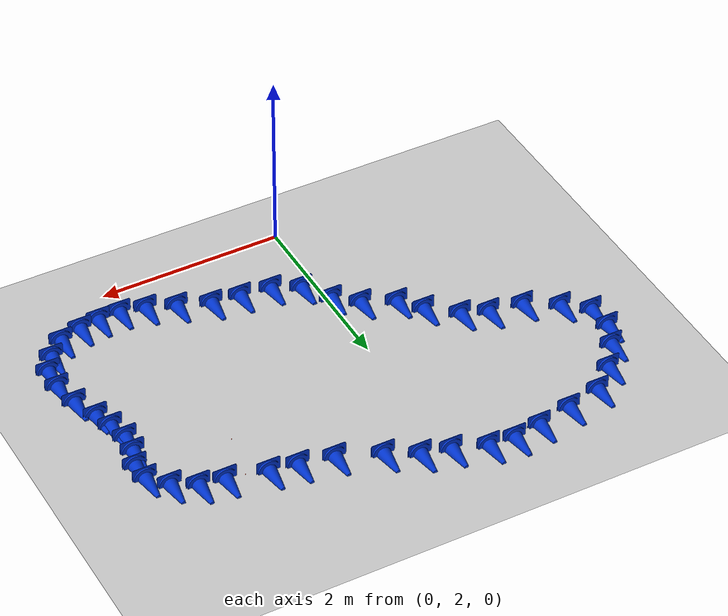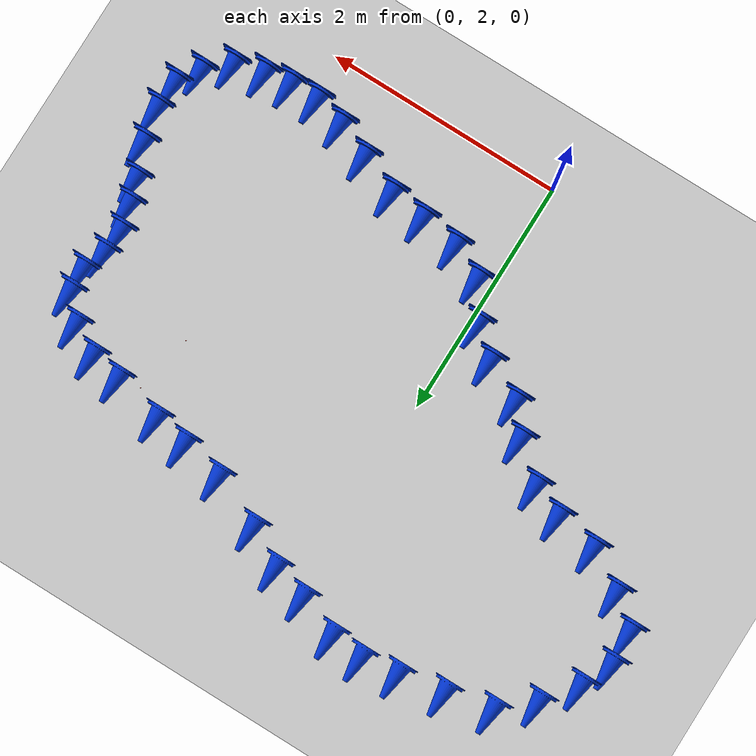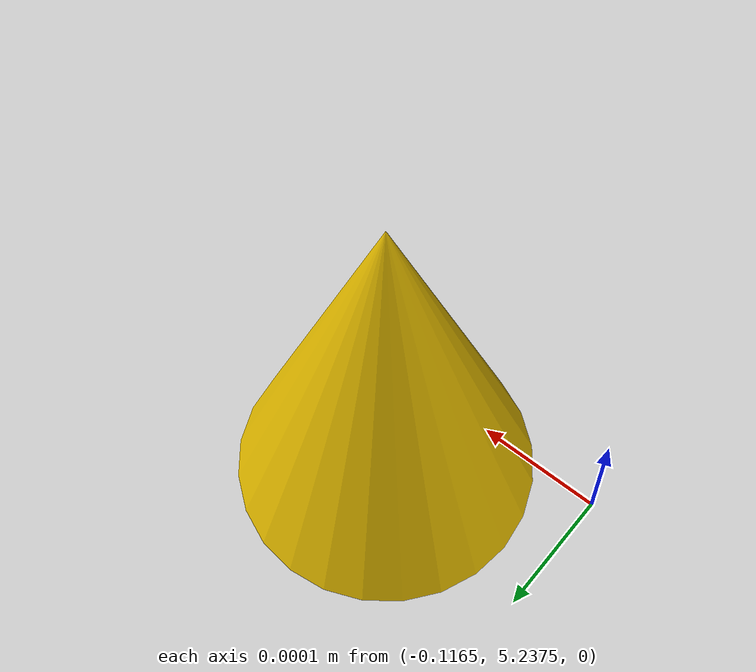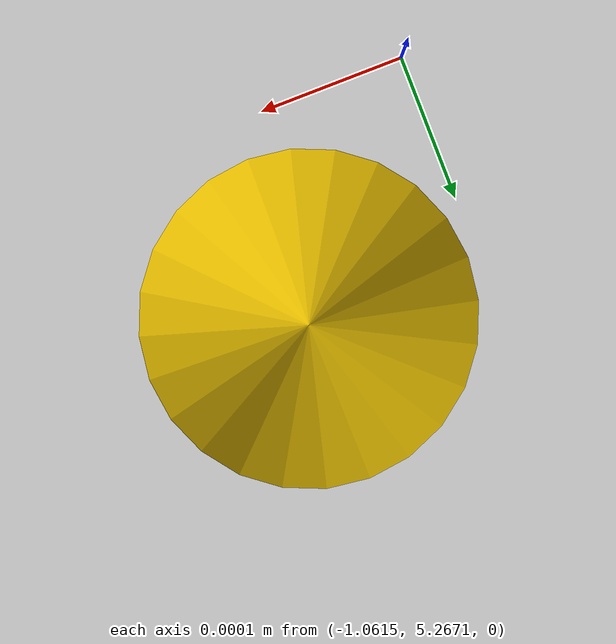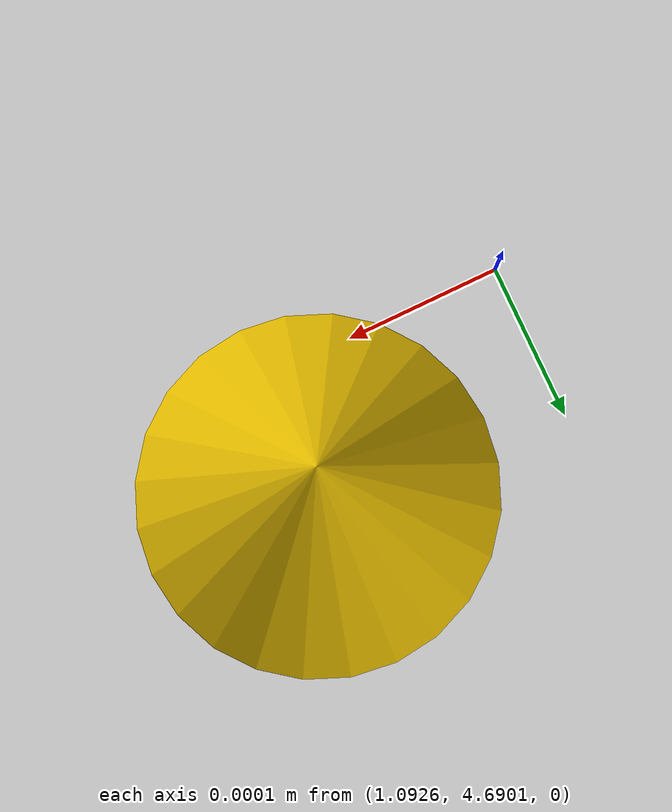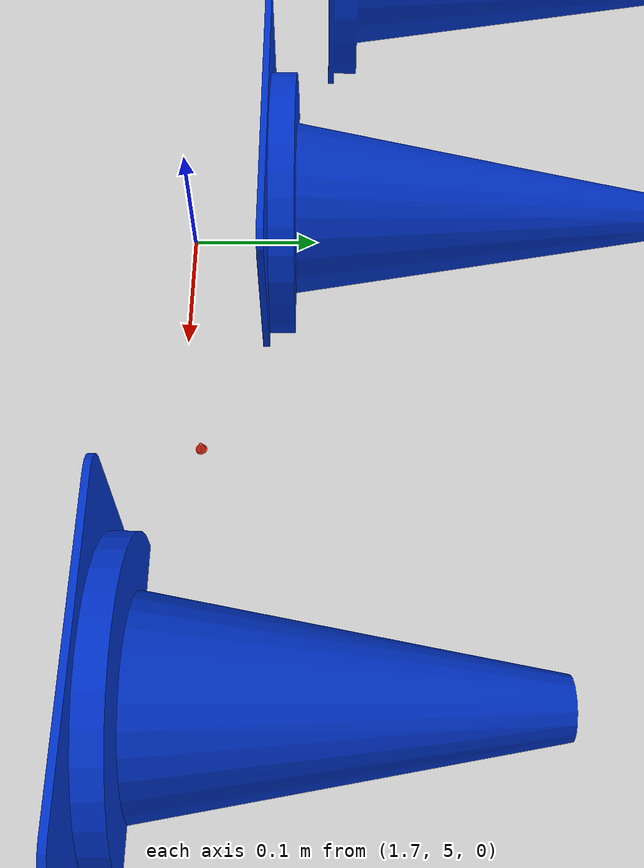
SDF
<sdf version="1.7">
 <world name="default">
  <light name="sun" type="directional">
   <pose>0 0 10 0 -0 0</pose>
   <diffuse>0.8 0.8 0.8 1</diffuse>
   <specular>0.2 0.2 0.2 1</specular>
   <attenuation>
    <range>1000</range>
    <constant>0.9</constant>
    <linear>0.01</linear>
    <quadratic>0.001</quadratic>
   </attenuation>
   <direction>-0.5 0.1 -0.9</direction>
   <spot><inner_angle>0</inner_angle><outer_angle>0</outer_angle><falloff>0</falloff></spot>
  </light>
  <model name="ground_plane">
   <static>1</static>
   <link name="link">
    <collision name="collision">
     <geometry><plane><normal>0 0 1</normal><size>100 100</size></plane></geometry>
     <surface><friction><ode><mu>100</mu><mu2>50</mu2></ode></friction></surface>
    </collision>
    <visual name="visual">
     <cast_shadows>0</cast_shadows>
     <geometry><plane><normal>0 0 1</normal><size>100 100</size></plane></geometry>
     <material>
      <script><uri>file://media/materials/scripts/gazebo.material</uri><name>Gazebo/Grey</name></script>
     </material>
    </visual>
   </link>
  </model>
  <gravity>0 0 -9.8</gravity>
  <magnetic_field>6e-06 2.3e-05 -4.2e-05</magnetic_field>
  <atmosphere type="adiabatic"/>
  <physics type="ode">
   <max_step_size>0.001</max_step_size>
   <real_time_factor>1</real_time_factor>
   <real_time_update_rate>1000</real_time_update_rate>
  </physics>
  <scene><ambient>0.4 0.4 0.4 1</ambient><background>0.7 0.7 0.7 1</background><shadows>1</shadows></scene>
  <audio><device>default</device></audio>
  <spherical_coordinates>
   <surface_model>EARTH_WGS84</surface_model>
   <latitude_deg>0</latitude_deg>
   <longitude_deg>0</longitude_deg>
   <elevation>0</elevation>
   <heading_deg>0</heading_deg>
  </spherical_coordinates>
  <model name="cone_blue">
   <static>1</static>
   <link name="link">
    <visual name="visual">
     <geometry><mesh><uri>model://cone_blue/meshes/cone.stl</uri><scale>0.001 0.001 0.001</scale></mesh></geometry>
     <material><ambient>0 0.2 0.8 1</ambient><diffuse>0 0.2 0.8 1</diffuse></material>
    </visual>
    <collision name="collision">
     <geometry><mesh><uri>model://cone_blue/meshes/cone.stl</uri><scale>0.001 0.001 0.001</scale></mesh></geometry>
    </collision>
    <inertial>
     <mass>0.1</mass>
     <inertia><ixx>0.0001</ixx><iyy>0.0001</iyy><izz>0.0001</izz><ixy>0</ixy><ixz>0</ixz><iyz>0</iyz></inertia>
    </inertial>
   </link>
   <pose>2.75031 3.78609 0 0 -0 0</pose>
  </model>
  <model name="cone_blue_0">
   <static>1</static>
   <link name="link">
    <visual name="visual">
     <geometry><mesh><uri>model://cone_blue/meshes/cone.stl</uri><scale>0.001 0.001 0.001</scale></mesh></geometry>
     <material><ambient>0 0.2 0.8 1</ambient><diffuse>0 0.2 0.8 1</diffuse></material>
    </visual>
    <collision name="collision">
     <geometry><mesh><uri>model://cone_blue/meshes/cone.stl</uri><scale>0.001 0.001 0.001</scale></mesh></geometry>
    </collision>
    <inertial>
     <mass>0.1</mass>
     <inertia><ixx>0.0001</ixx><iyy>0.0001</iyy><izz>0.0001</izz><ixy>0</ixy><ixz>0</ixz><iyz>0</iyz></inertia>
    </inertial>
   </link>
   <pose>2.8157 3.58631 0 0 -0 0</pose>
  </model>
  <model name="cone_blue_1">
   <static>1</static>
   <link name="link">
    <visual name="visual">
     <geometry><mesh><uri>model://cone_blue/meshes/cone.stl</uri><scale>0.001 0.001 0.001</scale></mesh></geometry>
     <material><ambient>0 0.2 0.8 1</ambient><diffuse>0 0.2 0.8 1</diffuse></material>
    </visual>
    <collision name="collision">
     <geometry><mesh><uri>model://cone_blue/meshes/cone.stl</uri><scale>0.001 0.001 0.001</scale></mesh></geometry>
    </collision>
    <inertial>
     <mass>0.1</mass>
     <inertia><ixx>0.0001</ixx><iyy>0.0001</iyy><izz>0.0001</izz><ixy>0</ixy><ixz>0</ixz><iyz>0</iyz></inertia>
    </inertial>
   </link>
   <pose>2.92114 3.31402 0 0 -0 0</pose>
  </model>
  <model name="cone_blue_2">
   <static>1</static>
   <link name="link">
    <visual name="visual">
     <geometry><mesh><uri>model://cone_blue/meshes/cone.stl</uri><scale>0.001 0.001 0.001</scale></mesh></geometry>
     <material><ambient>0 0.2 0.8 1</ambient><diffuse>0 0.2 0.8 1</diffuse></material>
    </visual>
    <collision name="collision">
     <geometry><mesh><uri>model://cone_blue/meshes/cone.stl</uri><scale>0.001 0.001 0.001</scale></mesh></geometry>
    </collision>
    <inertial>
     <mass>0.1</mass>
     <inertia><ixx>0.0001</ixx><iyy>0.0001</iyy><izz>0.0001</izz><ixy>0</ixy><ixz>0</ixz><iyz>0</iyz></inertia>
    </inertial>
   </link>
   <pose>2.97571 3.02533 0 0 -0 0</pose>
  </model>
  <model name="cone_blue_3">
   <static>1</static>
   <link name="link">
    <visual name="visual">
     <geometry><mesh><uri>model://cone_blue/meshes/cone.stl</uri><scale>0.001 0.001 0.001</scale></mesh></geometry>
     <material><ambient>0 0.2 0.8 1</ambient><diffuse>0 0.2 0.8 1</diffuse></material>
    </visual>
    <collision name="collision">
     <geometry><mesh><uri>model://cone_blue/meshes/cone.stl</uri><scale>0.001 0.001 0.001</scale></mesh></geometry>
    </collision>
    <inertial>
     <mass>0.1</mass>
     <inertia><ixx>0.0001</ixx><iyy>0.0001</iyy><izz>0.0001</izz><ixy>0</ixy><ixz>0</ixz><iyz>0</iyz></inertia>
    </inertial>
   </link>
   <pose>2.96296 2.78086 0 0 -0 0</pose>
  </model>
  <model name="cone_blue_4">
   <static>1</static>
   <link name="link">
    <visual name="visual">
     <geometry><mesh><uri>model://cone_blue/meshes/cone.stl</uri><scale>0.001 0.001 0.001</scale></mesh></geometry>
     <material><ambient>0 0.2 0.8 1</ambient><diffuse>0 0.2 0.8 1</diffuse></material>
    </visual>
    <collision name="collision">
     <geometry><mesh><uri>model://cone_blue/meshes/cone.stl</uri><scale>0.001 0.001 0.001</scale></mesh></geometry>
    </collision>
    <inertial>
     <mass>0.1</mass>
     <inertia><ixx>0.0001</ixx><iyy>0.0001</iyy><izz>0.0001</izz><ixy>0</ixy><ixz>0</ixz><iyz>0</iyz></inertia>
    </inertial>
   </link>
   <pose>2.69591 4.00096 0 0 -0 0</pose>
  </model>
  <model name="cone_blue_5">
   <static>1</static>
   <link name="link">
    <visual name="visual">
     <geometry><mesh><uri>model://cone_blue/meshes/cone.stl</uri><scale>0.001 0.001 0.001</scale></mesh></geometry>
     <material><ambient>0 0.2 0.8 1</ambient><diffuse>0 0.2 0.8 1</diffuse></material>
    </visual>
    <collision name="collision">
     <geometry><mesh><uri>model://cone_blue/meshes/cone.stl</uri><scale>0.001 0.001 0.001</scale></mesh></geometry>
    </collision>
    <inertial>
     <mass>0.1</mass>
     <inertia><ixx>0.0001</ixx><iyy>0.0001</iyy><izz>0.0001</izz><ixy>0</ixy><ixz>0</ixz><iyz>0</iyz></inertia>
    </inertial>
   </link>
   <pose>2.71277 4.21174 0 0 -0 0</pose>
  </model>
  <model name="cone_blue_6">
   <static>1</static>
   <link name="link">
    <visual name="visual">
     <geometry><mesh><uri>model://cone_blue/meshes/cone.stl</uri><scale>0.001 0.001 0.001</scale></mesh></geometry>
     <material><ambient>0 0.2 0.8 1</ambient><diffuse>0 0.2 0.8 1</diffuse></material>
    </visual>
    <collision name="collision">
     <geometry><mesh><uri>model://cone_blue/meshes/cone.stl</uri><scale>0.001 0.001 0.001</scale></mesh></geometry>
    </collision>
    <inertial>
     <mass>0.1</mass>
     <inertia><ixx>0.0001</ixx><iyy>0.0001</iyy><izz>0.0001</izz><ixy>0</ixy><ixz>0</ixz><iyz>0</iyz></inertia>
    </inertial>
   </link>
   <pose>2.78188 4.40944 0 0 -0 0</pose>
  </model>
  <model name="cone_blue_7">
   <static>1</static>
   <link name="link">
    <visual name="visual">
     <geometry><mesh><uri>model://cone_blue/meshes/cone.stl</uri><scale>0.001 0.001 0.001</scale></mesh></geometry>
     <material><ambient>0 0.2 0.8 1</ambient><diffuse>0 0.2 0.8 1</diffuse></material>
    </visual>
    <collision name="collision">
     <geometry><mesh><uri>model://cone_blue/meshes/cone.stl</uri><scale>0.001 0.001 0.001</scale></mesh></geometry>
    </collision>
    <inertial>
     <mass>0.1</mass>
     <inertia><ixx>0.0001</ixx><iyy>0.0001</iyy><izz>0.0001</izz><ixy>0</ixy><ixz>0</ixz><iyz>0</iyz></inertia>
    </inertial>
   </link>
   <pose>2.77037 4.60934 0 0 -0 0</pose>
  </model>
  <model name="cone_blue_8">
   <static>1</static>
   <link name="link">
    <visual name="visual">
     <geometry><mesh><uri>model://cone_blue/meshes/cone.stl</uri><scale>0.001 0.001 0.001</scale></mesh></geometry>
     <material><ambient>0 0.2 0.8 1</ambient><diffuse>0 0.2 0.8 1</diffuse></material>
    </visual>
    <collision name="collision">
     <geometry><mesh><uri>model://cone_blue/meshes/cone.stl</uri><scale>0.001 0.001 0.001</scale></mesh></geometry>
    </collision>
    <inertial>
     <mass>0.1</mass>
     <inertia><ixx>0.0001</ixx><iyy>0.0001</iyy><izz>0.0001</izz><ixy>0</ixy><ixz>0</ixz><iyz>0</iyz></inertia>
    </inertial>
   </link>
   <pose>2.59646 4.798 0 0 -0 0</pose>
  </model>
  <model name="cone_blue_9">
   <static>1</static>
   <link name="link">
    <visual name="visual">
     <geometry><mesh><uri>model://cone_blue/meshes/cone.stl</uri><scale>0.001 0.001 0.001</scale></mesh></geometry>
     <material><ambient>0 0.2 0.8 1</ambient><diffuse>0 0.2 0.8 1</diffuse></material>
    </visual>
    <collision name="collision">
     <geometry><mesh><uri>model://cone_blue/meshes/cone.stl</uri><scale>0.001 0.001 0.001</scale></mesh></geometry>
    </collision>
    <inertial>
     <mass>0.1</mass>
     <inertia><ixx>0.0001</ixx><iyy>0.0001</iyy><izz>0.0001</izz><ixy>0</ixy><ixz>0</ixz><iyz>0</iyz></inertia>
    </inertial>
   </link>
   <pose>2.35634 4.93302 0 0 -0 0</pose>
  </model>
  <model name="cone_blue_10">
   <static>1</static>
   <link name="link">
    <visual name="visual">
     <geometry><mesh><uri>model://cone_blue/meshes/cone.stl</uri><scale>0.001 0.001 0.001</scale></mesh></geometry>
     <material><ambient>0 0.2 0.8 1</ambient><diffuse>0 0.2 0.8 1</diffuse></material>
    </visual>
    <collision name="collision">
     <geometry><mesh><uri>model://cone_blue/meshes/cone.stl</uri><scale>0.001 0.001 0.001</scale></mesh></geometry>
    </collision>
    <inertial>
     <mass>0.1</mass>
     <inertia><ixx>0.0001</ixx><iyy>0.0001</iyy><izz>0.0001</izz><ixy>0</ixy><ixz>0</ixz><iyz>0</iyz></inertia>
    </inertial>
   </link>
   <pose>2.09426 4.98332 0 0 -0 0</pose>
  </model>
  <model name="cone_red">
   <static>1</static>
   <link name="link">
    <visual name="visual">
     <geometry><mesh><uri>model://cone_red/meshes/cone.stl</uri><scale>0.001 0.001 0.001</scale></mesh></geometry>
     <material><ambient>1 0.2 0.1 1</ambient><diffuse>1 0.2 0.1 1</diffuse></material>
    </visual>
    <collision name="collision">
     <geometry><mesh><uri>model://cone_red/meshes/cone.stl</uri><scale>0.001 0.001 0.001</scale></mesh></geometry>
    </collision>
    <inertial>
     <mass>0.1</mass>
     <inertia><ixx>0.0001</ixx><iyy>0.0001</iyy><izz>0.0001</izz><ixy>0</ixy><ixz>0</ixz><iyz>0</iyz></inertia>
    </inertial>
   </link>
   <pose>1.89743 5.01549 0 0 -0 0</pose>
  </model>
  <model name="cone_red_0">
   <static>1</static>
   <link name="link">
    <visual name="visual">
     <geometry><mesh><uri>model://cone_red/meshes/cone.stl</uri><scale>0.001 0.001 0.001</scale></mesh></geometry>
     <material><ambient>1 0.2 0.1 1</ambient><diffuse>1 0.2 0.1 1</diffuse></material>
    </visual>
    <collision name="collision">
     <geometry><mesh><uri>model://cone_red/meshes/cone.stl</uri><scale>0.001 0.001 0.001</scale></mesh></geometry>
    </collision>
    <inertial>
     <mass>0.1</mass>
     <inertia><ixx>0.0001</ixx><iyy>0.0001</iyy><izz>0.0001</izz><ixy>0</ixy><ixz>0</ixz><iyz>0</iyz></inertia>
    </inertial>
   </link>
   <pose>1.79661 4.51738 0 0 -0 0</pose>
  </model>
  <model name="cone_yellow">
   <static>1</static>
   <link name="link">
    <visual name="visual">
     <geometry>
      <mesh><uri>model://cone_yellow/meshes/cone.stl</uri><scale>0.001 0.001 0.001</scale></mesh>
     </geometry>
     <material><ambient>1 0.82 0 1</ambient><diffuse>1 0.82 0 1</diffuse></material>
    </visual>
    <collision name="collision">
     <geometry>
      <mesh><uri>model://cone_yellow/meshes/cone.stl</uri><scale>0.001 0.001 0.001</scale></mesh>
     </geometry>
    </collision>
    <inertial>
     <mass>0.1</mass>
     <inertia><ixx>0.0001</ixx><iyy>0.0001</iyy><izz>0.0001</izz><ixy>0</ixy><ixz>0</ixz><iyz>0</iyz></inertia>
    </inertial>
   </link>
   <pose>2.07551 4.49608 0 0 -0 0</pose>
  </model>
  <model name="cone_yellow_0">
   <static>1</static>
   <link name="link">
    <visual name="visual">
     <geometry>
      <mesh><uri>model://cone_yellow/meshes/cone.stl</uri><scale>0.001 0.001 0.001</scale></mesh>
     </geometry>
     <material><ambient>1 0.82 0 1</ambient><diffuse>1 0.82 0 1</diffuse></material>
    </visual>
    <collision name="collision">
     <geometry>
      <mesh><uri>model://cone_yellow/meshes/cone.stl</uri><scale>0.001 0.001 0.001</scale></mesh>
     </geometry>
    </collision>
    <inertial>
     <mass>0.1</mass>
     <inertia><ixx>0.0001</ixx><iyy>0.0001</iyy><izz>0.0001</izz><ixy>0</ixy><ixz>0</ixz><iyz>0</iyz></inertia>
    </inertial>
   </link>
   <pose>2.28787 4.43632 0 0 -0 0</pose>
  </model>
  <model name="cone_yellow_1">
   <static>1</static>
   <link name="link">
    <visual name="visual">
     <geometry>
      <mesh><uri>model://cone_yellow/meshes/cone.stl</uri><scale>0.001 0.001 0.001</scale></mesh>
     </geometry>
     <material><ambient>1 0.82 0 1</ambient><diffuse>1 0.82 0 1</diffuse></material>
    </visual>
    <collision name="collision">
     <geometry>
      <mesh><uri>model://cone_yellow/meshes/cone.stl</uri><scale>0.001 0.001 0.001</scale></mesh>
     </geometry>
    </collision>
    <inertial>
     <mass>0.1</mass>
     <inertia><ixx>0.0001</ixx><iyy>0.0001</iyy><izz>0.0001</izz><ixy>0</ixy><ixz>0</ixz><iyz>0</iyz></inertia>
    </inertial>
   </link>
   <pose>2.28726 4.23549 0 0 -0 0</pose>
  </model>
  <model name="cone_yellow_2">
   <static>1</static>
   <link name="link">
    <visual name="visual">
     <geometry>
      <mesh><uri>model://cone_yellow/meshes/cone.stl</uri><scale>0.001 0.001 0.001</scale></mesh>
     </geometry>
     <material><ambient>1 0.82 0 1</ambient><diffuse>1 0.82 0 1</diffuse></material>
    </visual>
    <collision name="collision">
     <geometry>
      <mesh><uri>model://cone_yellow/meshes/cone.stl</uri><scale>0.001 0.001 0.001</scale></mesh>
     </geometry>
    </collision>
    <inertial>
     <mass>0.1</mass>
     <inertia><ixx>0.0001</ixx><iyy>0.0001</iyy><izz>0.0001</izz><ixy>0</ixy><ixz>0</ixz><iyz>0</iyz></inertia>
    </inertial>
   </link>
   <pose>2.26198 4.03771 0 0 -0 0</pose>
  </model>
  <model name="cone_yellow_3">
   <static>1</static>
   <link name="link">
    <visual name="visual">
     <geometry>
      <mesh><uri>model://cone_yellow/meshes/cone.stl</uri><scale>0.001 0.001 0.001</scale></mesh>
     </geometry>
     <material><ambient>1 0.82 0 1</ambient><diffuse>1 0.82 0 1</diffuse></material>
    </visual>
    <collision name="collision">
     <geometry>
      <mesh><uri>model://cone_yellow/meshes/cone.stl</uri><scale>0.001 0.001 0.001</scale></mesh>
     </geometry>
    </collision>
    <inertial>
     <mass>0.1</mass>
     <inertia><ixx>0.0001</ixx><iyy>0.0001</iyy><izz>0.0001</izz><ixy>0</ixy><ixz>0</ixz><iyz>0</iyz></inertia>
    </inertial>
   </link>
   <pose>2.29638 3.82865 0 0 -0 0</pose>
  </model>
  <model name="cone_yellow_4">
   <static>1</static>
   <link name="link">
    <visual name="visual">
     <geometry>
      <mesh><uri>model://cone_yellow/meshes/cone.stl</uri><scale>0.001 0.001 0.001</scale></mesh>
     </geometry>
     <material><ambient>1 0.82 0 1</ambient><diffuse>1 0.82 0 1</diffuse></material>
    </visual>
    <collision name="collision">
     <geometry>
      <mesh><uri>model://cone_yellow/meshes/cone.stl</uri><scale>0.001 0.001 0.001</scale></mesh>
     </geometry>
    </collision>
    <inertial>
     <mass>0.1</mass>
     <inertia><ixx>0.0001</ixx><iyy>0.0001</iyy><izz>0.0001</izz><ixy>0</ixy><ixz>0</ixz><iyz>0</iyz></inertia>
    </inertial>
   </link>
   <pose>2.39422 3.6007 0 0 -0 0</pose>
  </model>
  <model name="cone_yellow_5">
   <static>1</static>
   <link name="link">
    <visual name="visual">
     <geometry>
      <mesh><uri>model://cone_yellow/meshes/cone.stl</uri><scale>0.001 0.001 0.001</scale></mesh>
     </geometry>
     <material><ambient>1 0.82 0 1</ambient><diffuse>1 0.82 0 1</diffuse></material>
    </visual>
    <collision name="collision">
     <geometry>
      <mesh><uri>model://cone_yellow/meshes/cone.stl</uri><scale>0.001 0.001 0.001</scale></mesh>
     </geometry>
    </collision>
    <inertial>
     <mass>0.1</mass>
     <inertia><ixx>0.0001</ixx><iyy>0.0001</iyy><izz>0.0001</izz><ixy>0</ixy><ixz>0</ixz><iyz>0</iyz></inertia>
    </inertial>
   </link>
   <pose>2.50956 3.3435 0 0 -0 0</pose>
  </model>
  <model name="cone_yellow_6">
   <static>1</static>
   <link name="link">
    <visual name="visual">
     <geometry>
      <mesh><uri>model://cone_yellow/meshes/cone.stl</uri><scale>0.001 0.001 0.001</scale></mesh>
     </geometry>
     <material><ambient>1 0.82 0 1</ambient><diffuse>1 0.82 0 1</diffuse></material>
    </visual>
    <collision name="collision">
     <geometry>
      <mesh><uri>model://cone_yellow/meshes/cone.stl</uri><scale>0.001 0.001 0.001</scale></mesh>
     </geometry>
    </collision>
    <inertial>
     <mass>0.1</mass>
     <inertia><ixx>0.0001</ixx><iyy>0.0001</iyy><izz>0.0001</izz><ixy>0</ixy><ixz>0</ixz><iyz>0</iyz></inertia>
    </inertial>
   </link>
   <pose>2.52169 3.03328 0 0 -0 0</pose>
  </model>
  <model name="cone_yellow_7">
   <static>1</static>
   <link name="link">
    <visual name="visual">
     <geometry>
      <mesh><uri>model://cone_yellow/meshes/cone.stl</uri><scale>0.001 0.001 0.001</scale></mesh>
     </geometry>
     <material><ambient>1 0.82 0 1</ambient><diffuse>1 0.82 0 1</diffuse></material>
    </visual>
    <collision name="collision">
     <geometry>
      <mesh><uri>model://cone_yellow/meshes/cone.stl</uri><scale>0.001 0.001 0.001</scale></mesh>
     </geometry>
    </collision>
    <inertial>
     <mass>0.1</mass>
     <inertia><ixx>0.0001</ixx><iyy>0.0001</iyy><izz>0.0001</izz><ixy>0</ixy><ixz>0</ixz><iyz>0</iyz></inertia>
    </inertial>
   </link>
   <pose>2.43952 2.81725 0 0 -0 0</pose>
  </model>
  <model name="cone_blue_11">
   <static>1</static>
   <link name="link">
    <visual name="visual">
     <geometry><mesh><uri>model://cone_blue/meshes/cone.stl</uri><scale>0.001 0.001 0.001</scale></mesh></geometry>
     <material><ambient>0 0.2 0.8 1</ambient><diffuse>0 0.2 0.8 1</diffuse></material>
    </visual>
    <collision name="collision">
     <geometry><mesh><uri>model://cone_blue/meshes/cone.stl</uri><scale>0.001 0.001 0.001</scale></mesh></geometry>
    </collision>
    <inertial>
     <mass>0.1</mass>
     <inertia><ixx>0.0001</ixx><iyy>0.0001</iyy><izz>0.0001</izz><ixy>0</ixy><ixz>0</ixz><iyz>0</iyz></inertia>
    </inertial>
   </link>
   <pose>2.84208 2.59534 0 0 -0 0</pose>
  </model>
  <model name="cone_blue_12">
   <static>1</static>
   <link name="link">
    <visual name="visual">
     <geometry><mesh><uri>model://cone_blue/meshes/cone.stl</uri><scale>0.001 0.001 0.001</scale></mesh></geometry>
     <material><ambient>0 0.2 0.8 1</ambient><diffuse>0 0.2 0.8 1</diffuse></material>
    </visual>
    <collision name="collision">
     <geometry><mesh><uri>model://cone_blue/meshes/cone.stl</uri><scale>0.001 0.001 0.001</scale></mesh></geometry>
    </collision>
    <inertial>
     <mass>0.1</mass>
     <inertia><ixx>0.0001</ixx><iyy>0.0001</iyy><izz>0.0001</izz><ixy>0</ixy><ixz>0</ixz><iyz>0</iyz></inertia>
    </inertial>
   </link>
   <pose>2.65559 2.41749 0 0 -0 0</pose>
  </model>
  <model name="cone_yellow_8">
   <static>1</static>
   <link name="link">
    <visual name="visual">
     <geometry>
      <mesh><uri>model://cone_yellow/meshes/cone.stl</uri><scale>0.001 0.001 0.001</scale></mesh>
     </geometry>
     <material><ambient>1 0.82 0 1</ambient><diffuse>1 0.82 0 1</diffuse></material>
    </visual>
    <collision name="collision">
     <geometry>
      <mesh><uri>model://cone_yellow/meshes/cone.stl</uri><scale>0.001 0.001 0.001</scale></mesh>
     </geometry>
    </collision>
    <inertial>
     <mass>0.1</mass>
     <inertia><ixx>0.0001</ixx><iyy>0.0001</iyy><izz>0.0001</izz><ixy>0</ixy><ixz>0</ixz><iyz>0</iyz></inertia>
    </inertial>
   </link>
   <pose>2.23773 2.78723 0 0 -0 0</pose>
  </model>
  <model name="cone_yellow_9">
   <static>1</static>
   <link name="link">
    <visual name="visual">
     <geometry>
      <mesh><uri>model://cone_yellow/meshes/cone.stl</uri><scale>0.001 0.001 0.001</scale></mesh>
     </geometry>
     <material><ambient>1 0.82 0 1</ambient><diffuse>1 0.82 0 1</diffuse></material>
    </visual>
    <collision name="collision">
     <geometry>
      <mesh><uri>model://cone_yellow/meshes/cone.stl</uri><scale>0.001 0.001 0.001</scale></mesh>
     </geometry>
    </collision>
    <inertial>
     <mass>0.1</mass>
     <inertia><ixx>0.0001</ixx><iyy>0.0001</iyy><izz>0.0001</izz><ixy>0</ixy><ixz>0</ixz><iyz>0</iyz></inertia>
    </inertial>
   </link>
   <pose>2.01111 2.76357 0 0 -0 0</pose>
  </model>
  <model name="cone_blue_13">
   <static>1</static>
   <link name="link">
    <visual name="visual">
     <geometry><mesh><uri>model://cone_blue/meshes/cone.stl</uri><scale>0.001 0.001 0.001</scale></mesh></geometry>
     <material><ambient>0 0.2 0.8 1</ambient><diffuse>0 0.2 0.8 1</diffuse></material>
    </visual>
    <collision name="collision">
     <geometry><mesh><uri>model://cone_blue/meshes/cone.stl</uri><scale>0.001 0.001 0.001</scale></mesh></geometry>
    </collision>
    <inertial>
     <mass>0.1</mass>
     <inertia><ixx>0.0001</ixx><iyy>0.0001</iyy><izz>0.0001</izz><ixy>0</ixy><ixz>0</ixz><iyz>0</iyz></inertia>
    </inertial>
   </link>
   <pose>2.41104 2.3445 0 0 -0 0</pose>
  </model>
  <model name="cone_blue_14">
   <static>1</static>
   <link name="link">
    <visual name="visual">
     <geometry><mesh><uri>model://cone_blue/meshes/cone.stl</uri><scale>0.001 0.001 0.001</scale></mesh></geometry>
     <material><ambient>0 0.2 0.8 1</ambient><diffuse>0 0.2 0.8 1</diffuse></material>
    </visual>
    <collision name="collision">
     <geometry><mesh><uri>model://cone_blue/meshes/cone.stl</uri><scale>0.001 0.001 0.001</scale></mesh></geometry>
    </collision>
    <inertial>
     <mass>0.1</mass>
     <inertia><ixx>0.0001</ixx><iyy>0.0001</iyy><izz>0.0001</izz><ixy>0</ixy><ixz>0</ixz><iyz>0</iyz></inertia>
    </inertial>
   </link>
   <pose>2.19078 2.30859 0 0 -0 0</pose>
  </model>
  <model name="cone_blue_15">
   <static>1</static>
   <link name="link">
    <visual name="visual">
     <geometry><mesh><uri>model://cone_blue/meshes/cone.stl</uri><scale>0.001 0.001 0.001</scale></mesh></geometry>
     <material><ambient>0 0.2 0.8 1</ambient><diffuse>0 0.2 0.8 1</diffuse></material>
    </visual>
    <collision name="collision">
     <geometry><mesh><uri>model://cone_blue/meshes/cone.stl</uri><scale>0.001 0.001 0.001</scale></mesh></geometry>
    </collision>
    <inertial>
     <mass>0.1</mass>
     <inertia><ixx>0.0001</ixx><iyy>0.0001</iyy><izz>0.0001</izz><ixy>0</ixy><ixz>0</ixz><iyz>0</iyz></inertia>
    </inertial>
   </link>
   <pose>1.95081 2.30327 0 0 -0 0</pose>
  </model>
  <model name="cone_yellow_10">
   <static>1</static>
   <link name="link">
    <visual name="visual">
     <geometry>
      <mesh><uri>model://cone_yellow/meshes/cone.stl</uri><scale>0.001 0.001 0.001</scale></mesh>
     </geometry>
     <material><ambient>1 0.82 0 1</ambient><diffuse>1 0.82 0 1</diffuse></material>
    </visual>
    <collision name="collision">
     <geometry>
      <mesh><uri>model://cone_yellow/meshes/cone.stl</uri><scale>0.001 0.001 0.001</scale></mesh>
     </geometry>
    </collision>
    <inertial>
     <mass>0.1</mass>
     <inertia><ixx>0.0001</ixx><iyy>0.0001</iyy><izz>0.0001</izz><ixy>0</ixy><ixz>0</ixz><iyz>0</iyz></inertia>
    </inertial>
   </link>
   <pose>1.75693 2.81616 0 0 -0 0</pose>
  </model>
  <model name="cone_yellow_11">
   <static>1</static>
   <link name="link">
    <visual name="visual">
     <geometry>
      <mesh><uri>model://cone_yellow/meshes/cone.stl</uri><scale>0.001 0.001 0.001</scale></mesh>
     </geometry>
     <material><ambient>1 0.82 0 1</ambient><diffuse>1 0.82 0 1</diffuse></material>
    </visual>
    <collision name="collision">
     <geometry>
      <mesh><uri>model://cone_yellow/meshes/cone.stl</uri><scale>0.001 0.001 0.001</scale></mesh>
     </geometry>
    </collision>
    <inertial>
     <mass>0.1</mass>
     <inertia><ixx>0.0001</ixx><iyy>0.0001</iyy><izz>0.0001</izz><ixy>0</ixy><ixz>0</ixz><iyz>0</iyz></inertia>
    </inertial>
   </link>
   <pose>1.45768 2.92805 0 0 -0 0</pose>
  </model>
  <model name="cone_yellow_12">
   <static>1</static>
   <link name="link">
    <visual name="visual">
     <geometry>
      <mesh><uri>model://cone_yellow/meshes/cone.stl</uri><scale>0.001 0.001 0.001</scale></mesh>
     </geometry>
     <material><ambient>1 0.82 0 1</ambient><diffuse>1 0.82 0 1</diffuse></material>
    </visual>
    <collision name="collision">
     <geometry>
      <mesh><uri>model://cone_yellow/meshes/cone.stl</uri><scale>0.001 0.001 0.001</scale></mesh>
     </geometry>
    </collision>
    <inertial>
     <mass>0.1</mass>
     <inertia><ixx>0.0001</ixx><iyy>0.0001</iyy><izz>0.0001</izz><ixy>0</ixy><ixz>0</ixz><iyz>0</iyz></inertia>
    </inertial>
   </link>
   <pose>1.13781 3.06278 0 0 -0 0</pose>
  </model>
  <model name="cone_yellow_13">
   <static>1</static>
   <link name="link">
    <visual name="visual">
     <geometry>
      <mesh><uri>model://cone_yellow/meshes/cone.stl</uri><scale>0.001 0.001 0.001</scale></mesh>
     </geometry>
     <material><ambient>1 0.82 0 1</ambient><diffuse>1 0.82 0 1</diffuse></material>
    </visual>
    <collision name="collision">
     <geometry>
      <mesh><uri>model://cone_yellow/meshes/cone.stl</uri><scale>0.001 0.001 0.001</scale></mesh>
     </geometry>
    </collision>
    <inertial>
     <mass>0.1</mass>
     <inertia><ixx>0.0001</ixx><iyy>0.0001</iyy><izz>0.0001</izz><ixy>0</ixy><ixz>0</ixz><iyz>0</iyz></inertia>
    </inertial>
   </link>
   <pose>0.794822 3.1223 0 0 -0 0</pose>
  </model>
  <model name="cone_blue_16">
   <static>1</static>
   <link name="link">
    <visual name="visual">
     <geometry><mesh><uri>model://cone_blue/meshes/cone.stl</uri><scale>0.001 0.001 0.001</scale></mesh></geometry>
     <material><ambient>0 0.2 0.8 1</ambient><diffuse>0 0.2 0.8 1</diffuse></material>
    </visual>
    <collision name="collision">
     <geometry><mesh><uri>model://cone_blue/meshes/cone.stl</uri><scale>0.001 0.001 0.001</scale></mesh></geometry>
    </collision>
    <inertial>
     <mass>0.1</mass>
     <inertia><ixx>0.0001</ixx><iyy>0.0001</iyy><izz>0.0001</izz><ixy>0</ixy><ixz>0</ixz><iyz>0</iyz></inertia>
    </inertial>
   </link>
   <pose>1.68811 2.36982 0 0 -0 0</pose>
  </model>
  <model name="cone_blue_17">
   <static>1</static>
   <link name="link">
    <visual name="visual">
     <geometry><mesh><uri>model://cone_blue/meshes/cone.stl</uri><scale>0.001 0.001 0.001</scale></mesh></geometry>
     <material><ambient>0 0.2 0.8 1</ambient><diffuse>0 0.2 0.8 1</diffuse></material>
    </visual>
    <collision name="collision">
     <geometry><mesh><uri>model://cone_blue/meshes/cone.stl</uri><scale>0.001 0.001 0.001</scale></mesh></geometry>
    </collision>
    <inertial>
     <mass>0.1</mass>
     <inertia><ixx>0.0001</ixx><iyy>0.0001</iyy><izz>0.0001</izz><ixy>0</ixy><ixz>0</ixz><iyz>0</iyz></inertia>
    </inertial>
   </link>
   <pose>1.39367 2.49002 0 0 -0 0</pose>
  </model>
  <model name="cone_blue_18">
   <static>1</static>
   <link name="link">
    <visual name="visual">
     <geometry><mesh><uri>model://cone_blue/meshes/cone.stl</uri><scale>0.001 0.001 0.001</scale></mesh></geometry>
     <material><ambient>0 0.2 0.8 1</ambient><diffuse>0 0.2 0.8 1</diffuse></material>
    </visual>
    <collision name="collision">
     <geometry><mesh><uri>model://cone_blue/meshes/cone.stl</uri><scale>0.001 0.001 0.001</scale></mesh></geometry>
    </collision>
    <inertial>
     <mass>0.1</mass>
     <inertia><ixx>0.0001</ixx><iyy>0.0001</iyy><izz>0.0001</izz><ixy>0</ixy><ixz>0</ixz><iyz>0</iyz></inertia>
    </inertial>
   </link>
   <pose>1.0613 2.61976 0 0 -0 0</pose>
  </model>
  <model name="cone_blue_19">
   <static>1</static>
   <link name="link">
    <visual name="visual">
     <geometry><mesh><uri>model://cone_blue/meshes/cone.stl</uri><scale>0.001 0.001 0.001</scale></mesh></geometry>
     <material><ambient>0 0.2 0.8 1</ambient><diffuse>0 0.2 0.8 1</diffuse></material>
    </visual>
    <collision name="collision">
     <geometry><mesh><uri>model://cone_blue/meshes/cone.stl</uri><scale>0.001 0.001 0.001</scale></mesh></geometry>
    </collision>
    <inertial>
     <mass>0.1</mass>
     <inertia><ixx>0.0001</ixx><iyy>0.0001</iyy><izz>0.0001</izz><ixy>0</ixy><ixz>0</ixz><iyz>0</iyz></inertia>
    </inertial>
   </link>
   <pose>0.751671 2.66171 0 0 -0 0</pose>
  </model>
  <model name="cone_blue_20">
   <static>1</static>
   <link name="link">
    <visual name="visual">
     <geometry><mesh><uri>model://cone_blue/meshes/cone.stl</uri><scale>0.001 0.001 0.001</scale></mesh></geometry>
     <material><ambient>0 0.2 0.8 1</ambient><diffuse>0 0.2 0.8 1</diffuse></material>
    </visual>
    <collision name="collision">
     <geometry><mesh><uri>model://cone_blue/meshes/cone.stl</uri><scale>0.001 0.001 0.001</scale></mesh></geometry>
    </collision>
    <inertial>
     <mass>0.1</mass>
     <inertia><ixx>0.0001</ixx><iyy>0.0001</iyy><izz>0.0001</izz><ixy>0</ixy><ixz>0</ixz><iyz>0</iyz></inertia>
    </inertial>
   </link>
   <pose>0.422435 2.70523 0 0 -0 0</pose>
  </model>
  <model name="cone_blue_21">
   <static>1</static>
   <link name="link">
    <visual name="visual">
     <geometry><mesh><uri>model://cone_blue/meshes/cone.stl</uri><scale>0.001 0.001 0.001</scale></mesh></geometry>
     <material><ambient>0 0.2 0.8 1</ambient><diffuse>0 0.2 0.8 1</diffuse></material>
    </visual>
    <collision name="collision">
     <geometry><mesh><uri>model://cone_blue/meshes/cone.stl</uri><scale>0.001 0.001 0.001</scale></mesh></geometry>
    </collision>
    <inertial>
     <mass>0.1</mass>
     <inertia><ixx>0.0001</ixx><iyy>0.0001</iyy><izz>0.0001</izz><ixy>0</ixy><ixz>0</ixz><iyz>0</iyz></inertia>
    </inertial>
   </link>
   <pose>0.136706 2.8434 0 0 -0 0</pose>
  </model>
  <model name="cone_blue_22">
   <static>1</static>
   <link name="link">
    <visual name="visual">
     <geometry><mesh><uri>model://cone_blue/meshes/cone.stl</uri><scale>0.001 0.001 0.001</scale></mesh></geometry>
     <material><ambient>0 0.2 0.8 1</ambient><diffuse>0 0.2 0.8 1</diffuse></material>
    </visual>
    <collision name="collision">
     <geometry><mesh><uri>model://cone_blue/meshes/cone.stl</uri><scale>0.001 0.001 0.001</scale></mesh></geometry>
    </collision>
    <inertial>
     <mass>0.1</mass>
     <inertia><ixx>0.0001</ixx><iyy>0.0001</iyy><izz>0.0001</izz><ixy>0</ixy><ixz>0</ixz><iyz>0</iyz></inertia>
    </inertial>
   </link>
   <pose>-0.051129 3.13741 0 0 -0 0</pose>
  </model>
  <model name="cone_blue_23">
   <static>1</static>
   <link name="link">
    <visual name="visual">
     <geometry><mesh><uri>model://cone_blue/meshes/cone.stl</uri><scale>0.001 0.001 0.001</scale></mesh></geometry>
     <material><ambient>0 0.2 0.8 1</ambient><diffuse>0 0.2 0.8 1</diffuse></material>
    </visual>
    <collision name="collision">
     <geometry><mesh><uri>model://cone_blue/meshes/cone.stl</uri><scale>0.001 0.001 0.001</scale></mesh></geometry>
    </collision>
    <inertial>
     <mass>0.1</mass>
     <inertia><ixx>0.0001</ixx><iyy>0.0001</iyy><izz>0.0001</izz><ixy>0</ixy><ixz>0</ixz><iyz>0</iyz></inertia>
    </inertial>
   </link>
   <pose>-0.285702 3.33716 0 0 -0 0</pose>
  </model>
  <model name="cone_blue_24">
   <static>1</static>
   <link name="link">
    <visual name="visual">
     <geometry><mesh><uri>model://cone_blue/meshes/cone.stl</uri><scale>0.001 0.001 0.001</scale></mesh></geometry>
     <material><ambient>0 0.2 0.8 1</ambient><diffuse>0 0.2 0.8 1</diffuse></material>
    </visual>
    <collision name="collision">
     <geometry><mesh><uri>model://cone_blue/meshes/cone.stl</uri><scale>0.001 0.001 0.001</scale></mesh></geometry>
    </collision>
    <inertial>
     <mass>0.1</mass>
     <inertia><ixx>0.0001</ixx><iyy>0.0001</iyy><izz>0.0001</izz><ixy>0</ixy><ixz>0</ixz><iyz>0</iyz></inertia>
    </inertial>
   </link>
   <pose>-0.619719 3.49818 0 0 -0 0</pose>
  </model>
  <model name="cone_blue_25">
   <static>1</static>
   <link name="link">
    <visual name="visual">
     <geometry><mesh><uri>model://cone_blue/meshes/cone.stl</uri><scale>0.001 0.001 0.001</scale></mesh></geometry>
     <material><ambient>0 0.2 0.8 1</ambient><diffuse>0 0.2 0.8 1</diffuse></material>
    </visual>
    <collision name="collision">
     <geometry><mesh><uri>model://cone_blue/meshes/cone.stl</uri><scale>0.001 0.001 0.001</scale></mesh></geometry>
    </collision>
    <inertial>
     <mass>0.1</mass>
     <inertia><ixx>0.0001</ixx><iyy>0.0001</iyy><izz>0.0001</izz><ixy>0</ixy><ixz>0</ixz><iyz>0</iyz></inertia>
    </inertial>
   </link>
   <pose>-0.805825 3.72733 0 0 -0 0</pose>
  </model>
  <model name="cone_blue_26">
   <static>1</static>
   <link name="link">
    <visual name="visual">
     <geometry><mesh><uri>model://cone_blue/meshes/cone.stl</uri><scale>0.001 0.001 0.001</scale></mesh></geometry>
     <material><ambient>0 0.2 0.8 1</ambient><diffuse>0 0.2 0.8 1</diffuse></material>
    </visual>
    <collision name="collision">
     <geometry><mesh><uri>model://cone_blue/meshes/cone.stl</uri><scale>0.001 0.001 0.001</scale></mesh></geometry>
    </collision>
    <inertial>
     <mass>0.1</mass>
     <inertia><ixx>0.0001</ixx><iyy>0.0001</iyy><izz>0.0001</izz><ixy>0</ixy><ixz>0</ixz><iyz>0</iyz></inertia>
    </inertial>
   </link>
   <pose>-1.09808 3.97022 0 0 -0 0</pose>
  </model>
  <model name="cone_blue_27">
   <static>1</static>
   <link name="link">
    <visual name="visual">
     <geometry><mesh><uri>model://cone_blue/meshes/cone.stl</uri><scale>0.001 0.001 0.001</scale></mesh></geometry>
     <material><ambient>0 0.2 0.8 1</ambient><diffuse>0 0.2 0.8 1</diffuse></material>
    </visual>
    <collision name="collision">
     <geometry><mesh><uri>model://cone_blue/meshes/cone.stl</uri><scale>0.001 0.001 0.001</scale></mesh></geometry>
    </collision>
    <inertial>
     <mass>0.1</mass>
     <inertia><ixx>0.0001</ixx><iyy>0.0001</iyy><izz>0.0001</izz><ixy>0</ixy><ixz>0</ixz><iyz>0</iyz></inertia>
    </inertial>
   </link>
   <pose>-1.36821 4.08062 0 0 -0 0</pose>
  </model>
  <model name="cone_blue_28">
   <static>1</static>
   <link name="link">
    <visual name="visual">
     <geometry><mesh><uri>model://cone_blue/meshes/cone.stl</uri><scale>0.001 0.001 0.001</scale></mesh></geometry>
     <material><ambient>0 0.2 0.8 1</ambient><diffuse>0 0.2 0.8 1</diffuse></material>
    </visual>
    <collision name="collision">
     <geometry><mesh><uri>model://cone_blue/meshes/cone.stl</uri><scale>0.001 0.001 0.001</scale></mesh></geometry>
    </collision>
    <inertial>
     <mass>0.1</mass>
     <inertia><ixx>0.0001</ixx><iyy>0.0001</iyy><izz>0.0001</izz><ixy>0</ixy><ixz>0</ixz><iyz>0</iyz></inertia>
    </inertial>
   </link>
   <pose>-1.72927 4.14752 0 0 -0 0</pose>
  </model>
  <model name="cone_blue_29">
   <static>1</static>
   <link name="link">
    <visual name="visual">
     <geometry><mesh><uri>model://cone_blue/meshes/cone.stl</uri><scale>0.001 0.001 0.001</scale></mesh></geometry>
     <material><ambient>0 0.2 0.8 1</ambient><diffuse>0 0.2 0.8 1</diffuse></material>
    </visual>
    <collision name="collision">
     <geometry><mesh><uri>model://cone_blue/meshes/cone.stl</uri><scale>0.001 0.001 0.001</scale></mesh></geometry>
    </collision>
    <inertial>
     <mass>0.1</mass>
     <inertia><ixx>0.0001</ixx><iyy>0.0001</iyy><izz>0.0001</izz><ixy>0</ixy><ixz>0</ixz><iyz>0</iyz></inertia>
    </inertial>
   </link>
   <pose>-2.06035 4.34593 0 0 -0 0</pose>
  </model>
  <model name="cone_blue_30">
   <static>1</static>
   <link name="link">
    <visual name="visual">
     <geometry><mesh><uri>model://cone_blue/meshes/cone.stl</uri><scale>0.001 0.001 0.001</scale></mesh></geometry>
     <material><ambient>0 0.2 0.8 1</ambient><diffuse>0 0.2 0.8 1</diffuse></material>
    </visual>
    <collision name="collision">
     <geometry><mesh><uri>model://cone_blue/meshes/cone.stl</uri><scale>0.001 0.001 0.001</scale></mesh></geometry>
    </collision>
    <inertial>
     <mass>0.1</mass>
     <inertia><ixx>0.0001</ixx><iyy>0.0001</iyy><izz>0.0001</izz><ixy>0</ixy><ixz>0</ixz><iyz>0</iyz></inertia>
    </inertial>
   </link>
   <pose>-2.30473 4.5487 0 0 -0 0</pose>
  </model>
  <model name="cone_blue_31">
   <static>1</static>
   <link name="link">
    <visual name="visual">
     <geometry><mesh><uri>model://cone_blue/meshes/cone.stl</uri><scale>0.001 0.001 0.001</scale></mesh></geometry>
     <material><ambient>0 0.2 0.8 1</ambient><diffuse>0 0.2 0.8 1</diffuse></material>
    </visual>
    <collision name="collision">
     <geometry><mesh><uri>model://cone_blue/meshes/cone.stl</uri><scale>0.001 0.001 0.001</scale></mesh></geometry>
    </collision>
    <inertial>
     <mass>0.1</mass>
     <inertia><ixx>0.0001</ixx><iyy>0.0001</iyy><izz>0.0001</izz><ixy>0</ixy><ixz>0</ixz><iyz>0</iyz></inertia>
    </inertial>
   </link>
   <pose>-2.31959 4.8354 0 0 -0 0</pose>
  </model>
  <model name="cone_blue_32">
   <static>1</static>
   <link name="link">
    <visual name="visual">
     <geometry><mesh><uri>model://cone_blue/meshes/cone.stl</uri><scale>0.001 0.001 0.001</scale></mesh></geometry>
     <material><ambient>0 0.2 0.8 1</ambient><diffuse>0 0.2 0.8 1</diffuse></material>
    </visual>
    <collision name="collision">
     <geometry><mesh><uri>model://cone_blue/meshes/cone.stl</uri><scale>0.001 0.001 0.001</scale></mesh></geometry>
    </collision>
    <inertial>
     <mass>0.1</mass>
     <inertia><ixx>0.0001</ixx><iyy>0.0001</iyy><izz>0.0001</izz><ixy>0</ixy><ixz>0</ixz><iyz>0</iyz></inertia>
    </inertial>
   </link>
   <pose>-2.20266 5.09677 0 0 -0 0</pose>
  </model>
  <model name="cone_yellow_14">
   <static>1</static>
   <link name="link">
    <visual name="visual">
     <geometry>
      <mesh><uri>model://cone_yellow/meshes/cone.stl</uri><scale>0.001 0.001 0.001</scale></mesh>
     </geometry>
     <material><ambient>1 0.82 0 1</ambient><diffuse>1 0.82 0 1</diffuse></material>
    </visual>
    <collision name="collision">
     <geometry>
      <mesh><uri>model://cone_yellow/meshes/cone.stl</uri><scale>0.001 0.001 0.001</scale></mesh>
     </geometry>
    </collision>
    <inertial>
     <mass>0.1</mass>
     <inertia><ixx>0.0001</ixx><iyy>0.0001</iyy><izz>0.0001</izz><ixy>0</ixy><ixz>0</ixz><iyz>0</iyz></inertia>
    </inertial>
   </link>
   <pose>0.487734 3.18719 0 0 -0 0</pose>
  </model>
  <model name="cone_yellow_15">
   <static>1</static>
   <link name="link">
    <visual name="visual">
     <geometry>
      <mesh><uri>model://cone_yellow/meshes/cone.stl</uri><scale>0.001 0.001 0.001</scale></mesh>
     </geometry>
     <material><ambient>1 0.82 0 1</ambient><diffuse>1 0.82 0 1</diffuse></material>
    </visual>
    <collision name="collision">
     <geometry>
      <mesh><uri>model://cone_yellow/meshes/cone.stl</uri><scale>0.001 0.001 0.001</scale></mesh>
     </geometry>
    </collision>
    <inertial>
     <mass>0.1</mass>
     <inertia><ixx>0.0001</ixx><iyy>0.0001</iyy><izz>0.0001</izz><ixy>0</ixy><ixz>0</ixz><iyz>0</iyz></inertia>
    </inertial>
   </link>
   <pose>0.281755 3.39213 0 0 -0 0</pose>
  </model>
  <model name="cone_yellow_16">
   <static>1</static>
   <link name="link">
    <visual name="visual">
     <geometry>
      <mesh><uri>model://cone_yellow/meshes/cone.stl</uri><scale>0.001 0.001 0.001</scale></mesh>
     </geometry>
     <material><ambient>1 0.82 0 1</ambient><diffuse>1 0.82 0 1</diffuse></material>
    </visual>
    <collision name="collision">
     <geometry>
      <mesh><uri>model://cone_yellow/meshes/cone.stl</uri><scale>0.001 0.001 0.001</scale></mesh>
     </geometry>
    </collision>
    <inertial>
     <mass>0.1</mass>
     <inertia><ixx>0.0001</ixx><iyy>0.0001</iyy><izz>0.0001</izz><ixy>0</ixy><ixz>0</ixz><iyz>0</iyz></inertia>
    </inertial>
   </link>
   <pose>0.02124 3.64062 0 0 -0 0</pose>
  </model>
  <model name="cone_yellow_17">
   <static>1</static>
   <link name="link">
    <visual name="visual">
     <geometry>
      <mesh><uri>model://cone_yellow/meshes/cone.stl</uri><scale>0.001 0.001 0.001</scale></mesh>
     </geometry>
     <material><ambient>1 0.82 0 1</ambient><diffuse>1 0.82 0 1</diffuse></material>
    </visual>
    <collision name="collision">
     <geometry>
      <mesh><uri>model://cone_yellow/meshes/cone.stl</uri><scale>0.001 0.001 0.001</scale></mesh>
     </geometry>
    </collision>
    <inertial>
     <mass>0.1</mass>
     <inertia><ixx>0.0001</ixx><iyy>0.0001</iyy><izz>0.0001</izz><ixy>0</ixy><ixz>0</ixz><iyz>0</iyz></inertia>
    </inertial>
   </link>
   <pose>-0.285726 3.82808 0 0 -0 0</pose>
  </model>
  <model name="cone_yellow_18">
   <static>1</static>
   <link name="link">
    <visual name="visual">
     <geometry>
      <mesh><uri>model://cone_yellow/meshes/cone.stl</uri><scale>0.001 0.001 0.001</scale></mesh>
     </geometry>
     <material><ambient>1 0.82 0 1</ambient><diffuse>1 0.82 0 1</diffuse></material>
    </visual>
    <collision name="collision">
     <geometry>
      <mesh><uri>model://cone_yellow/meshes/cone.stl</uri><scale>0.001 0.001 0.001</scale></mesh>
     </geometry>
    </collision>
    <inertial>
     <mass>0.1</mass>
     <inertia><ixx>0.0001</ixx><iyy>0.0001</iyy><izz>0.0001</izz><ixy>0</ixy><ixz>0</ixz><iyz>0</iyz></inertia>
    </inertial>
   </link>
   <pose>-0.510835 4.07299 0 0 -0 0</pose>
  </model>
  <model name="cone_yellow_19">
   <static>1</static>
   <link name="link">
    <visual name="visual">
     <geometry>
      <mesh><uri>model://cone_yellow/meshes/cone.stl</uri><scale>0.001 0.001 0.001</scale></mesh>
     </geometry>
     <material><ambient>1 0.82 0 1</ambient><diffuse>1 0.82 0 1</diffuse></material>
    </visual>
    <collision name="collision">
     <geometry>
      <mesh><uri>model://cone_yellow/meshes/cone.stl</uri><scale>0.001 0.001 0.001</scale></mesh>
     </geometry>
    </collision>
    <inertial>
     <mass>0.1</mass>
     <inertia><ixx>0.0001</ixx><iyy>0.0001</iyy><izz>0.0001</izz><ixy>0</ixy><ixz>0</ixz><iyz>0</iyz></inertia>
    </inertial>
   </link>
   <pose>-0.83399 4.28336 0 0 -0 0</pose>
  </model>
  <model name="cone_yellow_20">
   <static>1</static>
   <link name="link">
    <visual name="visual">
     <geometry>
      <mesh><uri>model://cone_yellow/meshes/cone.stl</uri><scale>0.001 0.001 0.001</scale></mesh>
     </geometry>
     <material><ambient>1 0.82 0 1</ambient><diffuse>1 0.82 0 1</diffuse></material>
    </visual>
    <collision name="collision">
     <geometry>
      <mesh><uri>model://cone_yellow/meshes/cone.stl</uri><scale>0.001 0.001 0.001</scale></mesh>
     </geometry>
    </collision>
    <inertial>
     <mass>0.1</mass>
     <inertia><ixx>0.0001</ixx><iyy>0.0001</iyy><izz>0.0001</izz><ixy>0</ixy><ixz>0</ixz><iyz>0</iyz></inertia>
    </inertial>
   </link>
   <pose>-1.19992 4.45414 0 0 -0 0</pose>
  </model>
  <model name="cone_yellow_21">
   <static>1</static>
   <link name="link">
    <visual name="visual">
     <geometry>
      <mesh><uri>model://cone_yellow/meshes/cone.stl</uri><scale>0.001 0.001 0.001</scale></mesh>
     </geometry>
     <material><ambient>1 0.82 0 1</ambient><diffuse>1 0.82 0 1</diffuse></material>
    </visual>
    <collision name="collision">
     <geometry>
      <mesh><uri>model://cone_yellow/meshes/cone.stl</uri><scale>0.001 0.001 0.001</scale></mesh>
     </geometry>
    </collision>
    <inertial>
     <mass>0.1</mass>
     <inertia><ixx>0.0001</ixx><iyy>0.0001</iyy><izz>0.0001</izz><ixy>0</ixy><ixz>0</ixz><iyz>0</iyz></inertia>
    </inertial>
   </link>
   <pose>-1.55045 4.5771 0 0 -0 0</pose>
  </model>
  <model name="cone_yellow_22">
   <static>1</static>
   <link name="link">
    <visual name="visual">
     <geometry>
      <mesh><uri>model://cone_yellow/meshes/cone.stl</uri><scale>0.001 0.001 0.001</scale></mesh>
     </geometry>
     <material><ambient>1 0.82 0 1</ambient><diffuse>1 0.82 0 1</diffuse></material>
    </visual>
    <collision name="collision">
     <geometry>
      <mesh><uri>model://cone_yellow/meshes/cone.stl</uri><scale>0.001 0.001 0.001</scale></mesh>
     </geometry>
    </collision>
    <inertial>
     <mass>0.1</mass>
     <inertia><ixx>0.0001</ixx><iyy>0.0001</iyy><izz>0.0001</izz><ixy>0</ixy><ixz>0</ixz><iyz>0</iyz></inertia>
    </inertial>
   </link>
   <pose>-1.75176 4.74814 0 0 -0 0</pose>
  </model>
  <model name="cone_yellow_23">
   <static>1</static>
   <link name="link">
    <visual name="visual">
     <geometry>
      <mesh><uri>model://cone_yellow/meshes/cone.stl</uri><scale>0.001 0.001 0.001</scale></mesh>
     </geometry>
     <material><ambient>1 0.82 0 1</ambient><diffuse>1 0.82 0 1</diffuse></material>
    </visual>
    <collision name="collision">
     <geometry>
      <mesh><uri>model://cone_yellow/meshes/cone.stl</uri><scale>0.001 0.001 0.001</scale></mesh>
     </geometry>
    </collision>
    <inertial>
     <mass>0.1</mass>
     <inertia><ixx>0.0001</ixx><iyy>0.0001</iyy><izz>0.0001</izz><ixy>0</ixy><ixz>0</ixz><iyz>0</iyz></inertia>
    </inertial>
   </link>
   <pose>-1.58244 5.00576 0 0 -0 0</pose>
  </model>
  <model name="cone_yellow_24">
   <static>1</static>
   <link name="link">
    <visual name="visual">
     <geometry>
      <mesh><uri>model://cone_yellow/meshes/cone.stl</uri><scale>0.001 0.001 0.001</scale></mesh>
     </geometry>
     <material><ambient>1 0.82 0 1</ambient><diffuse>1 0.82 0 1</diffuse></material>
    </visual>
    <collision name="collision">
     <geometry>
      <mesh><uri>model://cone_yellow/meshes/cone.stl</uri><scale>0.001 0.001 0.001</scale></mesh>
     </geometry>
    </collision>
    <inertial>
     <mass>0.1</mass>
     <inertia><ixx>0.0001</ixx><iyy>0.0001</iyy><izz>0.0001</izz><ixy>0</ixy><ixz>0</ixz><iyz>0</iyz></inertia>
    </inertial>
   </link>
   <pose>-1.31341 5.18976 0 0 -0 0</pose>
  </model>
  <model name="cone_yellow_25">
   <static>1</static>
   <link name="link">
    <visual name="visual">
     <geometry>
      <mesh><uri>model://cone_yellow/meshes/cone.stl</uri><scale>0.001 0.001 0.001</scale></mesh>
     </geometry>
     <material><ambient>1 0.82 0 1</ambient><diffuse>1 0.82 0 1</diffuse></material>
    </visual>
    <collision name="collision">
     <geometry>
      <mesh><uri>model://cone_yellow/meshes/cone.stl</uri><scale>0.001 0.001 0.001</scale></mesh>
     </geometry>
    </collision>
    <inertial>
     <mass>0.1</mass>
     <inertia><ixx>0.0001</ixx><iyy>0.0001</iyy><izz>0.0001</izz><ixy>0</ixy><ixz>0</ixz><iyz>0</iyz></inertia>
    </inertial>
   </link>
   <pose>-1.06138 5.26724 0 0 -0 0</pose>
  </model>
  <model name="cone_blue_33">
   <static>1</static>
   <link name="link">
    <visual name="visual">
     <geometry><mesh><uri>model://cone_blue/meshes/cone.stl</uri><scale>0.001 0.001 0.001</scale></mesh></geometry>
     <material><ambient>0 0.2 0.8 1</ambient><diffuse>0 0.2 0.8 1</diffuse></material>
    </visual>
    <collision name="collision">
     <geometry><mesh><uri>model://cone_blue/meshes/cone.stl</uri><scale>0.001 0.001 0.001</scale></mesh></geometry>
    </collision>
    <inertial>
     <mass>0.1</mass>
     <inertia><ixx>0.0001</ixx><iyy>0.0001</iyy><izz>0.0001</izz><ixy>0</ixy><ixz>0</ixz><iyz>0</iyz></inertia>
    </inertial>
   </link>
   <pose>-1.99337 5.37463 0 0 -0 0</pose>
  </model>
  <model name="cone_blue_34">
   <static>1</static>
   <link name="link">
    <visual name="visual">
     <geometry><mesh><uri>model://cone_blue/meshes/cone.stl</uri><scale>0.001 0.001 0.001</scale></mesh></geometry>
     <material><ambient>0 0.2 0.8 1</ambient><diffuse>0 0.2 0.8 1</diffuse></material>
    </visual>
    <collision name="collision">
     <geometry><mesh><uri>model://cone_blue/meshes/cone.stl</uri><scale>0.001 0.001 0.001</scale></mesh></geometry>
    </collision>
    <inertial>
     <mass>0.1</mass>
     <inertia><ixx>0.0001</ixx><iyy>0.0001</iyy><izz>0.0001</izz><ixy>0</ixy><ixz>0</ixz><iyz>0</iyz></inertia>
    </inertial>
   </link>
   <pose>-1.72686 5.60507 0 0 -0 0</pose>
  </model>
  <model name="cone_blue_35">
   <static>1</static>
   <link name="link">
    <visual name="visual">
     <geometry><mesh><uri>model://cone_blue/meshes/cone.stl</uri><scale>0.001 0.001 0.001</scale></mesh></geometry>
     <material><ambient>0 0.2 0.8 1</ambient><diffuse>0 0.2 0.8 1</diffuse></material>
    </visual>
    <collision name="collision">
     <geometry><mesh><uri>model://cone_blue/meshes/cone.stl</uri><scale>0.001 0.001 0.001</scale></mesh></geometry>
    </collision>
    <inertial>
     <mass>0.1</mass>
     <inertia><ixx>0.0001</ixx><iyy>0.0001</iyy><izz>0.0001</izz><ixy>0</ixy><ixz>0</ixz><iyz>0</iyz></inertia>
    </inertial>
   </link>
   <pose>-1.34085 5.69184 0 0 -0 0</pose>
  </model>
  <model name="cone_blue_36">
   <static>1</static>
   <link name="link">
    <visual name="visual">
     <geometry><mesh><uri>model://cone_blue/meshes/cone.stl</uri><scale>0.001 0.001 0.001</scale></mesh></geometry>
     <material><ambient>0 0.2 0.8 1</ambient><diffuse>0 0.2 0.8 1</diffuse></material>
    </visual>
    <collision name="collision">
     <geometry><mesh><uri>model://cone_blue/meshes/cone.stl</uri><scale>0.001 0.001 0.001</scale></mesh></geometry>
    </collision>
    <inertial>
     <mass>0.1</mass>
     <inertia><ixx>0.0001</ixx><iyy>0.0001</iyy><izz>0.0001</izz><ixy>0</ixy><ixz>0</ixz><iyz>0</iyz></inertia>
    </inertial>
   </link>
   <pose>-0.959184 5.76461 0 0 -0 0</pose>
  </model>
  <model name="cone_blue_37">
   <static>1</static>
   <link name="link">
    <visual name="visual">
     <geometry><mesh><uri>model://cone_blue/meshes/cone.stl</uri><scale>0.001 0.001 0.001</scale></mesh></geometry>
     <material><ambient>0 0.2 0.8 1</ambient><diffuse>0 0.2 0.8 1</diffuse></material>
    </visual>
    <collision name="collision">
     <geometry><mesh><uri>model://cone_blue/meshes/cone.stl</uri><scale>0.001 0.001 0.001</scale></mesh></geometry>
    </collision>
    <inertial>
     <mass>0.1</mass>
     <inertia><ixx>0.0001</ixx><iyy>0.0001</iyy><izz>0.0001</izz><ixy>0</ixy><ixz>0</ixz><iyz>0</iyz></inertia>
    </inertial>
   </link>
   <pose>-0.650761 5.80696 0 0 -0 0</pose>
  </model>
  <model name="cone_blue_38">
   <static>1</static>
   <link name="link">
    <visual name="visual">
     <geometry><mesh><uri>model://cone_blue/meshes/cone.stl</uri><scale>0.001 0.001 0.001</scale></mesh></geometry>
     <material><ambient>0 0.2 0.8 1</ambient><diffuse>0 0.2 0.8 1</diffuse></material>
    </visual>
    <collision name="collision">
     <geometry><mesh><uri>model://cone_blue/meshes/cone.stl</uri><scale>0.001 0.001 0.001</scale></mesh></geometry>
    </collision>
    <inertial>
     <mass>0.1</mass>
     <inertia><ixx>0.0001</ixx><iyy>0.0001</iyy><izz>0.0001</izz><ixy>0</ixy><ixz>0</ixz><iyz>0</iyz></inertia>
    </inertial>
   </link>
   <pose>-0.37267 5.78016 0 0 -0 0</pose>
  </model>
  <model name="cone_blue_39">
   <static>1</static>
   <link name="link">
    <visual name="visual">
     <geometry><mesh><uri>model://cone_blue/meshes/cone.stl</uri><scale>0.001 0.001 0.001</scale></mesh></geometry>
     <material><ambient>0 0.2 0.8 1</ambient><diffuse>0 0.2 0.8 1</diffuse></material>
    </visual>
    <collision name="collision">
     <geometry><mesh><uri>model://cone_blue/meshes/cone.stl</uri><scale>0.001 0.001 0.001</scale></mesh></geometry>
    </collision>
    <inertial>
     <mass>0.1</mass>
     <inertia><ixx>0.0001</ixx><iyy>0.0001</iyy><izz>0.0001</izz><ixy>0</ixy><ixz>0</ixz><iyz>0</iyz></inertia>
    </inertial>
   </link>
   <pose>-0.026108 5.6524 0 0 -0 0</pose>
  </model>
  <model name="cone_yellow_26">
   <static>1</static>
   <link name="link">
    <visual name="visual">
     <geometry>
      <mesh><uri>model://cone_yellow/meshes/cone.stl</uri><scale>0.001 0.001 0.001</scale></mesh>
     </geometry>
     <material><ambient>1 0.82 0 1</ambient><diffuse>1 0.82 0 1</diffuse></material>
    </visual>
    <collision name="collision">
     <geometry>
      <mesh><uri>model://cone_yellow/meshes/cone.stl</uri><scale>0.001 0.001 0.001</scale></mesh>
     </geometry>
    </collision>
    <inertial>
     <mass>0.1</mass>
     <inertia><ixx>0.0001</ixx><iyy>0.0001</iyy><izz>0.0001</izz><ixy>0</ixy><ixz>0</ixz><iyz>0</iyz></inertia>
    </inertial>
   </link>
   <pose>-0.791035 5.31732 0 0 -0 0</pose>
  </model>
  <model name="cone_yellow_27">
   <static>1</static>
   <link name="link">
    <visual name="visual">
     <geometry>
      <mesh><uri>model://cone_yellow/meshes/cone.stl</uri><scale>0.001 0.001 0.001</scale></mesh>
     </geometry>
     <material><ambient>1 0.82 0 1</ambient><diffuse>1 0.82 0 1</diffuse></material>
    </visual>
    <collision name="collision">
     <geometry>
      <mesh><uri>model://cone_yellow/meshes/cone.stl</uri><scale>0.001 0.001 0.001</scale></mesh>
     </geometry>
    </collision>
    <inertial>
     <mass>0.1</mass>
     <inertia><ixx>0.0001</ixx><iyy>0.0001</iyy><izz>0.0001</izz><ixy>0</ixy><ixz>0</ixz><iyz>0</iyz></inertia>
    </inertial>
   </link>
   <pose>-0.460315 5.29652 0 0 -0 0</pose>
  </model>
  <model name="cone_yellow_28">
   <static>1</static>
   <link name="link">
    <visual name="visual">
     <geometry>
      <mesh><uri>model://cone_yellow/meshes/cone.stl</uri><scale>0.001 0.001 0.001</scale></mesh>
     </geometry>
     <material><ambient>1 0.82 0 1</ambient><diffuse>1 0.82 0 1</diffuse></material>
    </visual>
    <collision name="collision">
     <geometry>
      <mesh><uri>model://cone_yellow/meshes/cone.stl</uri><scale>0.001 0.001 0.001</scale></mesh>
     </geometry>
    </collision>
    <inertial>
     <mass>0.1</mass>
     <inertia><ixx>0.0001</ixx><iyy>0.0001</iyy><izz>0.0001</izz><ixy>0</ixy><ixz>0</ixz><iyz>0</iyz></inertia>
    </inertial>
   </link>
   <pose>-0.116355 5.23757 0 0 -0 0</pose>
  </model>
  <model name="cone_yellow_29">
   <static>1</static>
   <link name="link">
    <visual name="visual">
     <geometry>
      <mesh><uri>model://cone_yellow/meshes/cone.stl</uri><scale>0.001 0.001 0.001</scale></mesh>
     </geometry>
     <material><ambient>1 0.82 0 1</ambient><diffuse>1 0.82 0 1</diffuse></material>
    </visual>
    <collision name="collision">
     <geometry>
      <mesh><uri>model://cone_yellow/meshes/cone.stl</uri><scale>0.001 0.001 0.001</scale></mesh>
     </geometry>
    </collision>
    <inertial>
     <mass>0.1</mass>
     <inertia><ixx>0.0001</ixx><iyy>0.0001</iyy><izz>0.0001</izz><ixy>0</ixy><ixz>0</ixz><iyz>0</iyz></inertia>
    </inertial>
   </link>
   <pose>0.152869 5.14826 0 0 -0 0</pose>
  </model>
  <model name="cone_yellow_30">
   <static>1</static>
   <link name="link">
    <visual name="visual">
     <geometry>
      <mesh><uri>model://cone_yellow/meshes/cone.stl</uri><scale>0.001 0.001 0.001</scale></mesh>
     </geometry>
     <material><ambient>1 0.82 0 1</ambient><diffuse>1 0.82 0 1</diffuse></material>
    </visual>
    <collision name="collision">
     <geometry>
      <mesh><uri>model://cone_yellow/meshes/cone.stl</uri><scale>0.001 0.001 0.001</scale></mesh>
     </geometry>
    </collision>
    <inertial>
     <mass>0.1</mass>
     <inertia><ixx>0.0001</ixx><iyy>0.0001</iyy><izz>0.0001</izz><ixy>0</ixy><ixz>0</ixz><iyz>0</iyz></inertia>
    </inertial>
   </link>
   <pose>0.406334 5.01781 0 0 -0 0</pose>
  </model>
  <model name="cone_blue_40">
   <static>1</static>
   <link name="link">
    <visual name="visual">
     <geometry><mesh><uri>model://cone_blue/meshes/cone.stl</uri><scale>0.001 0.001 0.001</scale></mesh></geometry>
     <material><ambient>0 0.2 0.8 1</ambient><diffuse>0 0.2 0.8 1</diffuse></material>
    </visual>
    <collision name="collision">
     <geometry><mesh><uri>model://cone_blue/meshes/cone.stl</uri><scale>0.001 0.001 0.001</scale></mesh></geometry>
    </collision>
    <inertial>
     <mass>0.1</mass>
     <inertia><ixx>0.0001</ixx><iyy>0.0001</iyy><izz>0.0001</izz><ixy>0</ixy><ixz>0</ixz><iyz>0</iyz></inertia>
    </inertial>
   </link>
   <pose>0.272662 5.56909 0 0 -0 0</pose>
  </model>
  <model name="cone_blue_41">
   <static>1</static>
   <link name="link">
    <visual name="visual">
     <geometry><mesh><uri>model://cone_blue/meshes/cone.stl</uri><scale>0.001 0.001 0.001</scale></mesh></geometry>
     <material><ambient>0 0.2 0.8 1</ambient><diffuse>0 0.2 0.8 1</diffuse></material>
    </visual>
    <collision name="collision">
     <geometry><mesh><uri>model://cone_blue/meshes/cone.stl</uri><scale>0.001 0.001 0.001</scale></mesh></geometry>
    </collision>
    <inertial>
     <mass>0.1</mass>
     <inertia><ixx>0.0001</ixx><iyy>0.0001</iyy><izz>0.0001</izz><ixy>0</ixy><ixz>0</ixz><iyz>0</iyz></inertia>
    </inertial>
   </link>
   <pose>0.587356 5.39833 0 0 -0 0</pose>
  </model>
  <model name="cone_blue_42">
   <static>1</static>
   <link name="link">
    <visual name="visual">
     <geometry><mesh><uri>model://cone_blue/meshes/cone.stl</uri><scale>0.001 0.001 0.001</scale></mesh></geometry>
     <material><ambient>0 0.2 0.8 1</ambient><diffuse>0 0.2 0.8 1</diffuse></material>
    </visual>
    <collision name="collision">
     <geometry><mesh><uri>model://cone_blue/meshes/cone.stl</uri><scale>0.001 0.001 0.001</scale></mesh></geometry>
    </collision>
    <inertial>
     <mass>0.1</mass>
     <inertia><ixx>0.0001</ixx><iyy>0.0001</iyy><izz>0.0001</izz><ixy>0</ixy><ixz>0</ixz><iyz>0</iyz></inertia>
    </inertial>
   </link>
   <pose>1.02391 5.21309 0 0 -0 0</pose>
  </model>
  <model name="cone_blue_43">
   <static>1</static>
   <link name="link">
    <visual name="visual">
     <geometry><mesh><uri>model://cone_blue/meshes/cone.stl</uri><scale>0.001 0.001 0.001</scale></mesh></geometry>
     <material><ambient>0 0.2 0.8 1</ambient><diffuse>0 0.2 0.8 1</diffuse></material>
    </visual>
    <collision name="collision">
     <geometry><mesh><uri>model://cone_blue/meshes/cone.stl</uri><scale>0.001 0.001 0.001</scale></mesh></geometry>
    </collision>
    <inertial>
     <mass>0.1</mass>
     <inertia><ixx>0.0001</ixx><iyy>0.0001</iyy><izz>0.0001</izz><ixy>0</ixy><ixz>0</ixz><iyz>0</iyz></inertia>
    </inertial>
   </link>
   <pose>1.38555 5.13464 0 0 -0 0</pose>
  </model>
  <model name="cone_blue_44">
   <static>1</static>
   <link name="link">
    <visual name="visual">
     <geometry><mesh><uri>model://cone_blue/meshes/cone.stl</uri><scale>0.001 0.001 0.001</scale></mesh></geometry>
     <material><ambient>0 0.2 0.8 1</ambient><diffuse>0 0.2 0.8 1</diffuse></material>
    </visual>
    <collision name="collision">
     <geometry><mesh><uri>model://cone_blue/meshes/cone.stl</uri><scale>0.001 0.001 0.001</scale></mesh></geometry>
    </collision>
    <inertial>
     <mass>0.1</mass>
     <inertia><ixx>0.0001</ixx><iyy>0.0001</iyy><izz>0.0001</izz><ixy>0</ixy><ixz>0</ixz><iyz>0</iyz></inertia>
    </inertial>
   </link>
   <pose>1.67387 5.08427 0 0 -0 0</pose>
  </model>
  <model name="cone_yellow_31">
   <static>1</static>
   <link name="link">
    <visual name="visual">
     <geometry>
      <mesh><uri>model://cone_yellow/meshes/cone.stl</uri><scale>0.001 0.001 0.001</scale></mesh>
     </geometry>
     <material><ambient>1 0.82 0 1</ambient><diffuse>1 0.82 0 1</diffuse></material>
    </visual>
    <collision name="collision">
     <geometry>
      <mesh><uri>model://cone_yellow/meshes/cone.stl</uri><scale>0.001 0.001 0.001</scale></mesh>
     </geometry>
    </collision>
    <inertial>
     <mass>0.1</mass>
     <inertia><ixx>0.0001</ixx><iyy>0.0001</iyy><izz>0.0001</izz><ixy>0</ixy><ixz>0</ixz><iyz>0</iyz></inertia>
    </inertial>
   </link>
   <pose>0.731633 4.87092 0 0 -0 0</pose>
  </model>
  <model name="cone_yellow_32">
   <static>1</static>
   <link name="link">
    <visual name="visual">
     <geometry>
      <mesh><uri>model://cone_yellow/meshes/cone.stl</uri><scale>0.001 0.001 0.001</scale></mesh>
     </geometry>
     <material><ambient>1 0.82 0 1</ambient><diffuse>1 0.82 0 1</diffuse></material>
    </visual>
    <collision name="collision">
     <geometry>
      <mesh><uri>model://cone_yellow/meshes/cone.stl</uri><scale>0.001 0.001 0.001</scale></mesh>
     </geometry>
    </collision>
    <inertial>
     <mass>0.1</mass>
     <inertia><ixx>0.0001</ixx><iyy>0.0001</iyy><izz>0.0001</izz><ixy>0</ixy><ixz>0</ixz><iyz>0</iyz></inertia>
    </inertial>
   </link>
   <pose>1.09276 4.69018 0 0 -0 0</pose>
  </model>
  <model name="cone_yellow_33">
   <static>1</static>
   <link name="link">
    <visual name="visual">
     <geometry>
      <mesh><uri>model://cone_yellow/meshes/cone.stl</uri><scale>0.001 0.001 0.001</scale></mesh>
     </geometry>
     <material><ambient>1 0.82 0 1</ambient><diffuse>1 0.82 0 1</diffuse></material>
    </visual>
    <collision name="collision">
     <geometry>
      <mesh><uri>model://cone_yellow/meshes/cone.stl</uri><scale>0.001 0.001 0.001</scale></mesh>
     </geometry>
    </collision>
    <inertial>
     <mass>0.1</mass>
     <inertia><ixx>0.0001</ixx><iyy>0.0001</iyy><izz>0.0001</izz><ixy>0</ixy><ixz>0</ixz><iyz>0</iyz></inertia>
    </inertial>
   </link>
   <pose>1.43949 4.59454 0 0 -0 0</pose>
  </model>
 </world>
</sdf>
